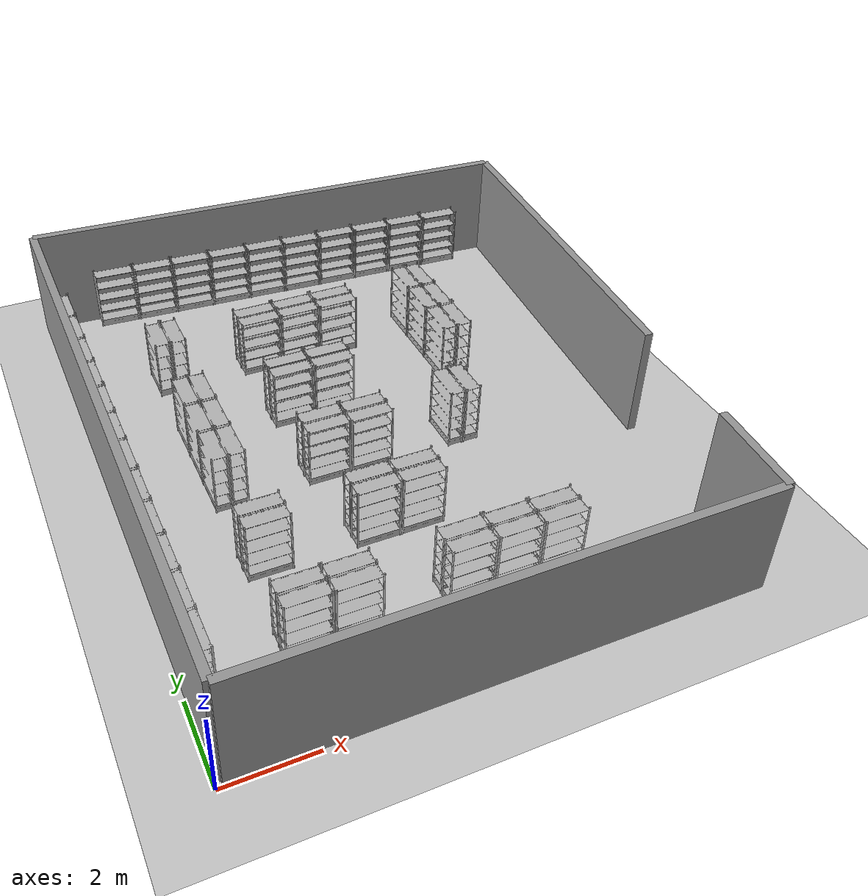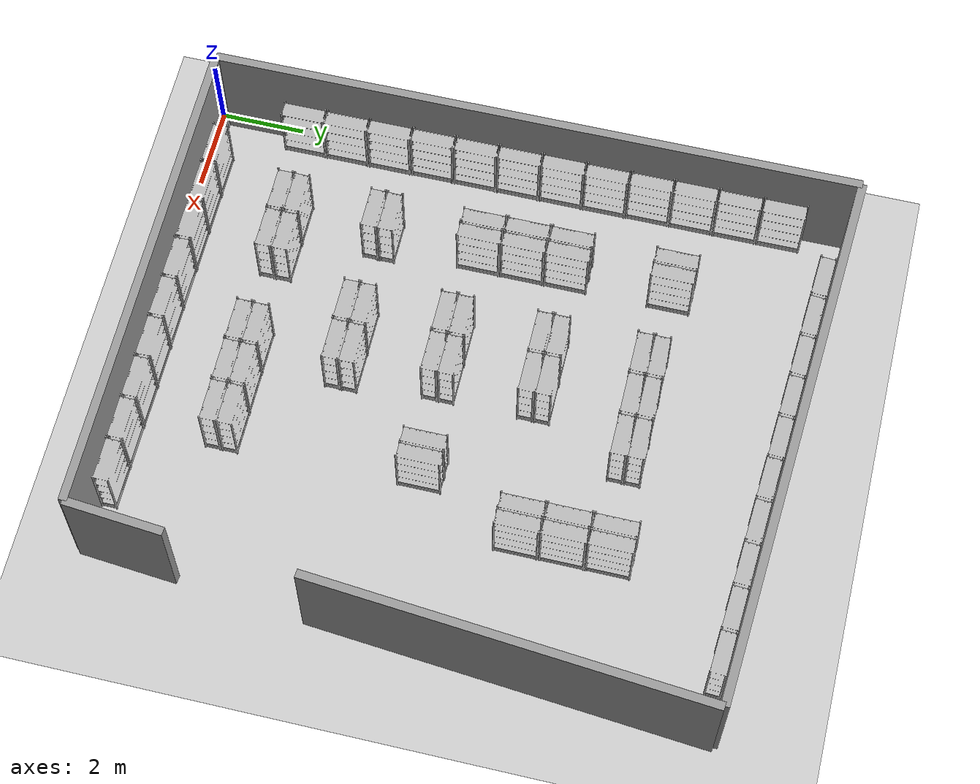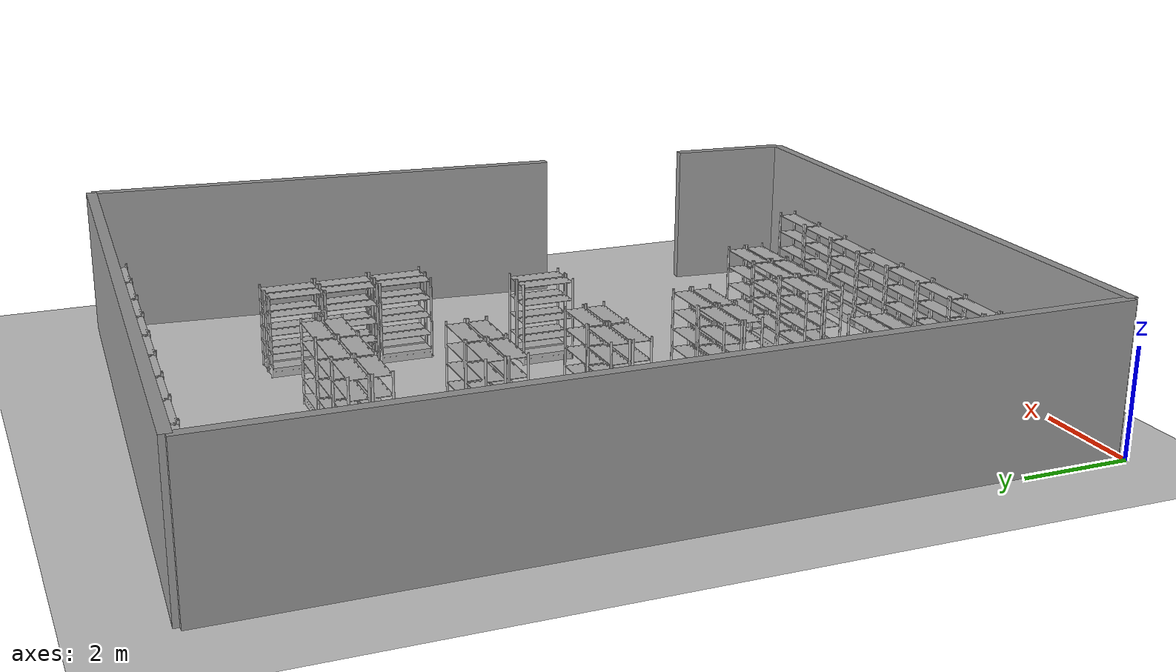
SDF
<sdf version="1.6">
  <world name="default">
    <light name="sun" type="directional">
      <cast_shadows>1</cast_shadows>
      <pose frame="">0 0 10 0 -0 0</pose>
      <diffuse>0.8 0.8 0.8 1</diffuse>
      <specular>0.2 0.2 0.2 1</specular>
      <attenuation>
        <range>1000</range>
        <constant>0.9</constant>
        <linear>0.01</linear>
        <quadratic>0.001</quadratic>
      </attenuation>
      <direction>-0.5 0.1 -0.9</direction>
    </light>
    <model name="ground_plane">
      <static>1</static>
      <link name="link">
        <collision name="collision">
          <geometry>
            <plane>
              <normal>0 0 1</normal>
              <size>100 100</size>
            </plane>
          </geometry>
          <surface>
            <contact>
              <collide_bitmask>65535</collide_bitmask>
              <ode />
            </contact>
            <friction>
              <ode>
                <mu>1000</mu>
                <mu2>1000</mu2>
              </ode>
              <torsional>
                <ode />
              </torsional>
            </friction>
            <bounce />
          </surface>
          <max_contacts>10</max_contacts>
        </collision>
        <visual name="visual">
          <cast_shadows>0</cast_shadows>
          <geometry>
            <plane>
              <normal>0 0 1</normal>
              <size>100 100</size>
            </plane>
          </geometry>
          <material>
            <script>
              <uri>file://media/materials/scripts/gazebo.material</uri>
              <name>Gazebo/Grey</name>
            </script>
          </material>
        </visual>
        <self_collide>0</self_collide>
        <enable_wind>0</enable_wind>
        <kinematic>0</kinematic>
      </link>
    </model>
    <gravity>0 0 -9.8</gravity>
    <magnetic_field>6e-06 2.3e-05 -4.2e-05</magnetic_field>
    <atmosphere type="adiabatic" />
    <physics name="default_physics" default="0" type="ode">
      <max_step_size>0.001</max_step_size>
      <real_time_factor>1</real_time_factor>
      <real_time_update_rate>1000</real_time_update_rate>
    </physics>
    <scene>
      <ambient>0.4 0.4 0.4 1</ambient>
      <background>0.7 0.7 0.7 1</background>
      <shadows>1</shadows>
    </scene>
    <audio>
      <device>default</device>
    </audio>
    <wind />
    <spherical_coordinates>
      <surface_model>EARTH_WGS84</surface_model>
      <latitude_deg>0</latitude_deg>
      <longitude_deg>0</longitude_deg>
      <elevation>0</elevation>
      <heading_deg>0</heading_deg>
    </spherical_coordinates>
    <gui fullscreen="0">
      <camera name="user_camera">
        <pose frame="">5.5458 -17.3868 19.7357 0 0.841797 1.67218</pose>
        <view_controller>orbit</view_controller>
        <projection_type>perspective</projection_type>
      </camera>
    </gui>
    <plugin name="ActorPosesPlugin" filename="libActorPosesPlugin.so" />
    <model name="store_shelf_moduled_0">
      <link name="link">
        <collision name="collision">
          <geometry>
            <mesh>
              <uri>model://store_shelf_moduled/meshes/store_shelf_moduled.dae</uri>
            </mesh>
          </geometry>
        </collision>
        <visual name="visual">
          <geometry>
            <mesh>
              <uri>model://store_shelf_moduled/meshes/store_shelf_moduled.dae</uri>
            </mesh>
          </geometry>
        </visual>
        <inertial>
          <mass>1000</mass>
          <inertia>
            <ixx>840083</ixx>
            <ixy>0</ixy>
            <ixz>0</ixz>
            <iyy>475500</iyy>
            <iyz>0</iyz>
            <izz>1.30208e+06</izz>
          </inertia>
        </inertial>
        <self_collide>0</self_collide>
        <enable_wind>0</enable_wind>
        <kinematic>0</kinematic>
      </link>
      <static>1</static>
      <pose frame="">1.180256 0.2199997 0 0 0 -0.002564097</pose>
    </model>
    <model name="store_shelf_moduled_1">
      <link name="link">
        <collision name="collision">
          <geometry>
            <mesh>
              <uri>model://store_shelf_moduled/meshes/store_shelf_moduled.dae</uri>
            </mesh>
          </geometry>
        </collision>
        <visual name="visual">
          <geometry>
            <mesh>
              <uri>model://store_shelf_moduled/meshes/store_shelf_moduled.dae</uri>
            </mesh>
          </geometry>
        </visual>
        <inertial>
          <mass>1000</mass>
          <inertia>
            <ixx>840083</ixx>
            <ixy>0</ixy>
            <ixz>0</ixz>
            <iyy>475500</iyy>
            <iyz>0</iyz>
            <izz>1.30208e+06</izz>
          </inertia>
        </inertial>
        <self_collide>0</self_collide>
        <enable_wind>0</enable_wind>
        <kinematic>0</kinematic>
      </link>
      <static>1</static>
      <pose frame="">2.240256 0.2199997 0 0 0 -0.002564097</pose>
    </model>
    <model name="store_shelf_moduled_2">
      <link name="link">
        <collision name="collision">
          <geometry>
            <mesh>
              <uri>model://store_shelf_moduled/meshes/store_shelf_moduled.dae</uri>
            </mesh>
          </geometry>
        </collision>
        <visual name="visual">
          <geometry>
            <mesh>
              <uri>model://store_shelf_moduled/meshes/store_shelf_moduled.dae</uri>
            </mesh>
          </geometry>
        </visual>
        <inertial>
          <mass>1000</mass>
          <inertia>
            <ixx>840083</ixx>
            <ixy>0</ixy>
            <ixz>0</ixz>
            <iyy>475500</iyy>
            <iyz>0</iyz>
            <izz>1.30208e+06</izz>
          </inertia>
        </inertial>
        <self_collide>0</self_collide>
        <enable_wind>0</enable_wind>
        <kinematic>0</kinematic>
      </link>
      <static>1</static>
      <pose frame="">3.300256 0.2199997 0 0 0 -0.002564097</pose>
    </model>
    <model name="store_shelf_moduled_3">
      <link name="link">
        <collision name="collision">
          <geometry>
            <mesh>
              <uri>model://store_shelf_moduled/meshes/store_shelf_moduled.dae</uri>
            </mesh>
          </geometry>
        </collision>
        <visual name="visual">
          <geometry>
            <mesh>
              <uri>model://store_shelf_moduled/meshes/store_shelf_moduled.dae</uri>
            </mesh>
          </geometry>
        </visual>
        <inertial>
          <mass>1000</mass>
          <inertia>
            <ixx>840083</ixx>
            <ixy>0</ixy>
            <ixz>0</ixz>
            <iyy>475500</iyy>
            <iyz>0</iyz>
            <izz>1.30208e+06</izz>
          </inertia>
        </inertial>
        <self_collide>0</self_collide>
        <enable_wind>0</enable_wind>
        <kinematic>0</kinematic>
      </link>
      <static>1</static>
      <pose frame="">4.360256 0.2099997 0 0 0 -0.002564097</pose>
    </model>
    <model name="store_shelf_moduled_4">
      <link name="link">
        <collision name="collision">
          <geometry>
            <mesh>
              <uri>model://store_shelf_moduled/meshes/store_shelf_moduled.dae</uri>
            </mesh>
          </geometry>
        </collision>
        <visual name="visual">
          <geometry>
            <mesh>
              <uri>model://store_shelf_moduled/meshes/store_shelf_moduled.dae</uri>
            </mesh>
          </geometry>
        </visual>
        <inertial>
          <mass>1000</mass>
          <inertia>
            <ixx>840083</ixx>
            <ixy>0</ixy>
            <ixz>0</ixz>
            <iyy>475500</iyy>
            <iyz>0</iyz>
            <izz>1.30208e+06</izz>
          </inertia>
        </inertial>
        <self_collide>0</self_collide>
        <enable_wind>0</enable_wind>
        <kinematic>0</kinematic>
      </link>
      <static>1</static>
      <pose frame="">5.420256 0.2099997 0 0 0 -0.002564097</pose>
    </model>
    <model name="store_shelf_moduled_5">
      <link name="link">
        <collision name="collision">
          <geometry>
            <mesh>
              <uri>model://store_shelf_moduled/meshes/store_shelf_moduled.dae</uri>
            </mesh>
          </geometry>
        </collision>
        <visual name="visual">
          <geometry>
            <mesh>
              <uri>model://store_shelf_moduled/meshes/store_shelf_moduled.dae</uri>
            </mesh>
          </geometry>
        </visual>
        <inertial>
          <mass>1000</mass>
          <inertia>
            <ixx>840083</ixx>
            <ixy>0</ixy>
            <ixz>0</ixz>
            <iyy>475500</iyy>
            <iyz>0</iyz>
            <izz>1.30208e+06</izz>
          </inertia>
        </inertial>
        <self_collide>0</self_collide>
        <enable_wind>0</enable_wind>
        <kinematic>0</kinematic>
      </link>
      <static>1</static>
      <pose frame="">6.480257 0.2099997 0 0 0 -0.002564097</pose>
    </model>
    <model name="store_shelf_moduled_6">
      <link name="link">
        <collision name="collision">
          <geometry>
            <mesh>
              <uri>model://store_shelf_moduled/meshes/store_shelf_moduled.dae</uri>
            </mesh>
          </geometry>
        </collision>
        <visual name="visual">
          <geometry>
            <mesh>
              <uri>model://store_shelf_moduled/meshes/store_shelf_moduled.dae</uri>
            </mesh>
          </geometry>
        </visual>
        <inertial>
          <mass>1000</mass>
          <inertia>
            <ixx>840083</ixx>
            <ixy>0</ixy>
            <ixz>0</ixz>
            <iyy>475500</iyy>
            <iyz>0</iyz>
            <izz>1.30208e+06</izz>
          </inertia>
        </inertial>
        <self_collide>0</self_collide>
        <enable_wind>0</enable_wind>
        <kinematic>0</kinematic>
      </link>
      <static>1</static>
      <pose frame="">7.540257 0.2099997 0 0 0 -0.002564097</pose>
    </model>
    <model name="store_shelf_moduled_7">
      <link name="link">
        <collision name="collision">
          <geometry>
            <mesh>
              <uri>model://store_shelf_moduled/meshes/store_shelf_moduled.dae</uri>
            </mesh>
          </geometry>
        </collision>
        <visual name="visual">
          <geometry>
            <mesh>
              <uri>model://store_shelf_moduled/meshes/store_shelf_moduled.dae</uri>
            </mesh>
          </geometry>
        </visual>
        <inertial>
          <mass>1000</mass>
          <inertia>
            <ixx>840083</ixx>
            <ixy>0</ixy>
            <ixz>0</ixz>
            <iyy>475500</iyy>
            <iyz>0</iyz>
            <izz>1.30208e+06</izz>
          </inertia>
        </inertial>
        <self_collide>0</self_collide>
        <enable_wind>0</enable_wind>
        <kinematic>0</kinematic>
      </link>
      <static>1</static>
      <pose frame="">8.600256 0.1999997 0 0 0 -0.002564097</pose>
    </model>
    <model name="store_shelf_moduled_8">
      <link name="link">
        <collision name="collision">
          <geometry>
            <mesh>
              <uri>model://store_shelf_moduled/meshes/store_shelf_moduled.dae</uri>
            </mesh>
          </geometry>
        </collision>
        <visual name="visual">
          <geometry>
            <mesh>
              <uri>model://store_shelf_moduled/meshes/store_shelf_moduled.dae</uri>
            </mesh>
          </geometry>
        </visual>
        <inertial>
          <mass>1000</mass>
          <inertia>
            <ixx>840083</ixx>
            <ixy>0</ixy>
            <ixz>0</ixz>
            <iyy>475500</iyy>
            <iyz>0</iyz>
            <izz>1.30208e+06</izz>
          </inertia>
        </inertial>
        <self_collide>0</self_collide>
        <enable_wind>0</enable_wind>
        <kinematic>0</kinematic>
      </link>
      <static>1</static>
      <pose frame="">9.660256 0.1999997 0 0 0 -0.002564097</pose>
    </model>
    <model name="store_shelf_moduled_9">
      <link name="link">
        <collision name="collision">
          <geometry>
            <mesh>
              <uri>model://store_shelf_moduled/meshes/store_shelf_moduled.dae</uri>
            </mesh>
          </geometry>
        </collision>
        <visual name="visual">
          <geometry>
            <mesh>
              <uri>model://store_shelf_moduled/meshes/store_shelf_moduled.dae</uri>
            </mesh>
          </geometry>
        </visual>
        <inertial>
          <mass>1000</mass>
          <inertia>
            <ixx>840083</ixx>
            <ixy>0</ixy>
            <ixz>0</ixz>
            <iyy>475500</iyy>
            <iyz>0</iyz>
            <izz>1.30208e+06</izz>
          </inertia>
        </inertial>
        <self_collide>0</self_collide>
        <enable_wind>0</enable_wind>
        <kinematic>0</kinematic>
      </link>
      <static>1</static>
      <pose frame="">12.02416 14.70017 0 0 0 3.083153</pose>
    </model>
    <model name="store_shelf_moduled_10">
      <link name="link">
        <collision name="collision">
          <geometry>
            <mesh>
              <uri>model://store_shelf_moduled/meshes/store_shelf_moduled.dae</uri>
            </mesh>
          </geometry>
        </collision>
        <visual name="visual">
          <geometry>
            <mesh>
              <uri>model://store_shelf_moduled/meshes/store_shelf_moduled.dae</uri>
            </mesh>
          </geometry>
        </visual>
        <inertial>
          <mass>1000</mass>
          <inertia>
            <ixx>840083</ixx>
            <ixy>0</ixy>
            <ixz>0</ixz>
            <iyy>475500</iyy>
            <iyz>0</iyz>
            <izz>1.30208e+06</izz>
          </inertia>
        </inertial>
        <self_collide>0</self_collide>
        <enable_wind>0</enable_wind>
        <kinematic>0</kinematic>
      </link>
      <static>1</static>
      <pose frame="">10.96416 14.76017 0 0 0 3.083153</pose>
    </model>
    <model name="store_shelf_moduled_11">
      <link name="link">
        <collision name="collision">
          <geometry>
            <mesh>
              <uri>model://store_shelf_moduled/meshes/store_shelf_moduled.dae</uri>
            </mesh>
          </geometry>
        </collision>
        <visual name="visual">
          <geometry>
            <mesh>
              <uri>model://store_shelf_moduled/meshes/store_shelf_moduled.dae</uri>
            </mesh>
          </geometry>
        </visual>
        <inertial>
          <mass>1000</mass>
          <inertia>
            <ixx>840083</ixx>
            <ixy>0</ixy>
            <ixz>0</ixz>
            <iyy>475500</iyy>
            <iyz>0</iyz>
            <izz>1.30208e+06</izz>
          </inertia>
        </inertial>
        <self_collide>0</self_collide>
        <enable_wind>0</enable_wind>
        <kinematic>0</kinematic>
      </link>
      <static>1</static>
      <pose frame="">9.90416 14.82017 0 0 0 3.083153</pose>
    </model>
    <model name="store_shelf_moduled_12">
      <link name="link">
        <collision name="collision">
          <geometry>
            <mesh>
              <uri>model://store_shelf_moduled/meshes/store_shelf_moduled.dae</uri>
            </mesh>
          </geometry>
        </collision>
        <visual name="visual">
          <geometry>
            <mesh>
              <uri>model://store_shelf_moduled/meshes/store_shelf_moduled.dae</uri>
            </mesh>
          </geometry>
        </visual>
        <inertial>
          <mass>1000</mass>
          <inertia>
            <ixx>840083</ixx>
            <ixy>0</ixy>
            <ixz>0</ixz>
            <iyy>475500</iyy>
            <iyz>0</iyz>
            <izz>1.30208e+06</izz>
          </inertia>
        </inertial>
        <self_collide>0</self_collide>
        <enable_wind>0</enable_wind>
        <kinematic>0</kinematic>
      </link>
      <static>1</static>
      <pose frame="">8.844159 14.88017 0 0 0 3.083153</pose>
    </model>
    <model name="store_shelf_moduled_13">
      <link name="link">
        <collision name="collision">
          <geometry>
            <mesh>
              <uri>model://store_shelf_moduled/meshes/store_shelf_moduled.dae</uri>
            </mesh>
          </geometry>
        </collision>
        <visual name="visual">
          <geometry>
            <mesh>
              <uri>model://store_shelf_moduled/meshes/store_shelf_moduled.dae</uri>
            </mesh>
          </geometry>
        </visual>
        <inertial>
          <mass>1000</mass>
          <inertia>
            <ixx>840083</ixx>
            <ixy>0</ixy>
            <ixz>0</ixz>
            <iyy>475500</iyy>
            <iyz>0</iyz>
            <izz>1.30208e+06</izz>
          </inertia>
        </inertial>
        <self_collide>0</self_collide>
        <enable_wind>0</enable_wind>
        <kinematic>0</kinematic>
      </link>
      <static>1</static>
      <pose frame="">7.78416 14.94017 0 0 0 3.083153</pose>
    </model>
    <model name="store_shelf_moduled_14">
      <link name="link">
        <collision name="collision">
          <geometry>
            <mesh>
              <uri>model://store_shelf_moduled/meshes/store_shelf_moduled.dae</uri>
            </mesh>
          </geometry>
        </collision>
        <visual name="visual">
          <geometry>
            <mesh>
              <uri>model://store_shelf_moduled/meshes/store_shelf_moduled.dae</uri>
            </mesh>
          </geometry>
        </visual>
        <inertial>
          <mass>1000</mass>
          <inertia>
            <ixx>840083</ixx>
            <ixy>0</ixy>
            <ixz>0</ixz>
            <iyy>475500</iyy>
            <iyz>0</iyz>
            <izz>1.30208e+06</izz>
          </inertia>
        </inertial>
        <self_collide>0</self_collide>
        <enable_wind>0</enable_wind>
        <kinematic>0</kinematic>
      </link>
      <static>1</static>
      <pose frame="">6.734159 15.01017 0 0 0 3.083153</pose>
    </model>
    <model name="store_shelf_moduled_15">
      <link name="link">
        <collision name="collision">
          <geometry>
            <mesh>
              <uri>model://store_shelf_moduled/meshes/store_shelf_moduled.dae</uri>
            </mesh>
          </geometry>
        </collision>
        <visual name="visual">
          <geometry>
            <mesh>
              <uri>model://store_shelf_moduled/meshes/store_shelf_moduled.dae</uri>
            </mesh>
          </geometry>
        </visual>
        <inertial>
          <mass>1000</mass>
          <inertia>
            <ixx>840083</ixx>
            <ixy>0</ixy>
            <ixz>0</ixz>
            <iyy>475500</iyy>
            <iyz>0</iyz>
            <izz>1.30208e+06</izz>
          </inertia>
        </inertial>
        <self_collide>0</self_collide>
        <enable_wind>0</enable_wind>
        <kinematic>0</kinematic>
      </link>
      <static>1</static>
      <pose frame="">5.67416 15.07017 0 0 0 3.083153</pose>
    </model>
    <model name="store_shelf_moduled_16">
      <link name="link">
        <collision name="collision">
          <geometry>
            <mesh>
              <uri>model://store_shelf_moduled/meshes/store_shelf_moduled.dae</uri>
            </mesh>
          </geometry>
        </collision>
        <visual name="visual">
          <geometry>
            <mesh>
              <uri>model://store_shelf_moduled/meshes/store_shelf_moduled.dae</uri>
            </mesh>
          </geometry>
        </visual>
        <inertial>
          <mass>1000</mass>
          <inertia>
            <ixx>840083</ixx>
            <ixy>0</ixy>
            <ixz>0</ixz>
            <iyy>475500</iyy>
            <iyz>0</iyz>
            <izz>1.30208e+06</izz>
          </inertia>
        </inertial>
        <self_collide>0</self_collide>
        <enable_wind>0</enable_wind>
        <kinematic>0</kinematic>
      </link>
      <static>1</static>
      <pose frame="">4.614159 15.13017 0 0 0 3.083153</pose>
    </model>
    <model name="store_shelf_moduled_17">
      <link name="link">
        <collision name="collision">
          <geometry>
            <mesh>
              <uri>model://store_shelf_moduled/meshes/store_shelf_moduled.dae</uri>
            </mesh>
          </geometry>
        </collision>
        <visual name="visual">
          <geometry>
            <mesh>
              <uri>model://store_shelf_moduled/meshes/store_shelf_moduled.dae</uri>
            </mesh>
          </geometry>
        </visual>
        <inertial>
          <mass>1000</mass>
          <inertia>
            <ixx>840083</ixx>
            <ixy>0</ixy>
            <ixz>0</ixz>
            <iyy>475500</iyy>
            <iyz>0</iyz>
            <izz>1.30208e+06</izz>
          </inertia>
        </inertial>
        <self_collide>0</self_collide>
        <enable_wind>0</enable_wind>
        <kinematic>0</kinematic>
      </link>
      <static>1</static>
      <pose frame="">3.554159 15.19017 0 0 0 3.083153</pose>
    </model>
    <model name="store_shelf_moduled_18">
      <link name="link">
        <collision name="collision">
          <geometry>
            <mesh>
              <uri>model://store_shelf_moduled/meshes/store_shelf_moduled.dae</uri>
            </mesh>
          </geometry>
        </collision>
        <visual name="visual">
          <geometry>
            <mesh>
              <uri>model://store_shelf_moduled/meshes/store_shelf_moduled.dae</uri>
            </mesh>
          </geometry>
        </visual>
        <inertial>
          <mass>1000</mass>
          <inertia>
            <ixx>840083</ixx>
            <ixy>0</ixy>
            <ixz>0</ixz>
            <iyy>475500</iyy>
            <iyz>0</iyz>
            <izz>1.30208e+06</izz>
          </inertia>
        </inertial>
        <self_collide>0</self_collide>
        <enable_wind>0</enable_wind>
        <kinematic>0</kinematic>
      </link>
      <static>1</static>
      <pose frame="">2.494159 15.25017 0 0 0 3.083153</pose>
    </model>
    <model name="store_shelf_moduled_19">
      <link name="link">
        <collision name="collision">
          <geometry>
            <mesh>
              <uri>model://store_shelf_moduled/meshes/store_shelf_moduled.dae</uri>
            </mesh>
          </geometry>
        </collision>
        <visual name="visual">
          <geometry>
            <mesh>
              <uri>model://store_shelf_moduled/meshes/store_shelf_moduled.dae</uri>
            </mesh>
          </geometry>
        </visual>
        <inertial>
          <mass>1000</mass>
          <inertia>
            <ixx>840083</ixx>
            <ixy>0</ixy>
            <ixz>0</ixz>
            <iyy>475500</iyy>
            <iyz>0</iyz>
            <izz>1.30208e+06</izz>
          </inertia>
        </inertial>
        <self_collide>0</self_collide>
        <enable_wind>0</enable_wind>
        <kinematic>0</kinematic>
      </link>
      <static>1</static>
      <pose frame="">0.1999998 14.4402 0 0 0 -1.568844</pose>
    </model>
    <model name="store_shelf_moduled_20">
      <link name="link">
        <collision name="collision">
          <geometry>
            <mesh>
              <uri>model://store_shelf_moduled/meshes/store_shelf_moduled.dae</uri>
            </mesh>
          </geometry>
        </collision>
        <visual name="visual">
          <geometry>
            <mesh>
              <uri>model://store_shelf_moduled/meshes/store_shelf_moduled.dae</uri>
            </mesh>
          </geometry>
        </visual>
        <inertial>
          <mass>1000</mass>
          <inertia>
            <ixx>840083</ixx>
            <ixy>0</ixy>
            <ixz>0</ixz>
            <iyy>475500</iyy>
            <iyz>0</iyz>
            <izz>1.30208e+06</izz>
          </inertia>
        </inertial>
        <self_collide>0</self_collide>
        <enable_wind>0</enable_wind>
        <kinematic>0</kinematic>
      </link>
      <static>1</static>
      <pose frame="">0.1999998 13.3802 0 0 0 -1.568844</pose>
    </model>
    <model name="store_shelf_moduled_21">
      <link name="link">
        <collision name="collision">
          <geometry>
            <mesh>
              <uri>model://store_shelf_moduled/meshes/store_shelf_moduled.dae</uri>
            </mesh>
          </geometry>
        </collision>
        <visual name="visual">
          <geometry>
            <mesh>
              <uri>model://store_shelf_moduled/meshes/store_shelf_moduled.dae</uri>
            </mesh>
          </geometry>
        </visual>
        <inertial>
          <mass>1000</mass>
          <inertia>
            <ixx>840083</ixx>
            <ixy>0</ixy>
            <ixz>0</ixz>
            <iyy>475500</iyy>
            <iyz>0</iyz>
            <izz>1.30208e+06</izz>
          </inertia>
        </inertial>
        <self_collide>0</self_collide>
        <enable_wind>0</enable_wind>
        <kinematic>0</kinematic>
      </link>
      <static>1</static>
      <pose frame="">0.1999998 12.3202 0 0 0 -1.568844</pose>
    </model>
    <model name="store_shelf_moduled_22">
      <link name="link">
        <collision name="collision">
          <geometry>
            <mesh>
              <uri>model://store_shelf_moduled/meshes/store_shelf_moduled.dae</uri>
            </mesh>
          </geometry>
        </collision>
        <visual name="visual">
          <geometry>
            <mesh>
              <uri>model://store_shelf_moduled/meshes/store_shelf_moduled.dae</uri>
            </mesh>
          </geometry>
        </visual>
        <inertial>
          <mass>1000</mass>
          <inertia>
            <ixx>840083</ixx>
            <ixy>0</ixy>
            <ixz>0</ixz>
            <iyy>475500</iyy>
            <iyz>0</iyz>
            <izz>1.30208e+06</izz>
          </inertia>
        </inertial>
        <self_collide>0</self_collide>
        <enable_wind>0</enable_wind>
        <kinematic>0</kinematic>
      </link>
      <static>1</static>
      <pose frame="">0.1999998 11.2602 0 0 0 -1.568844</pose>
    </model>
    <model name="store_shelf_moduled_23">
      <link name="link">
        <collision name="collision">
          <geometry>
            <mesh>
              <uri>model://store_shelf_moduled/meshes/store_shelf_moduled.dae</uri>
            </mesh>
          </geometry>
        </collision>
        <visual name="visual">
          <geometry>
            <mesh>
              <uri>model://store_shelf_moduled/meshes/store_shelf_moduled.dae</uri>
            </mesh>
          </geometry>
        </visual>
        <inertial>
          <mass>1000</mass>
          <inertia>
            <ixx>840083</ixx>
            <ixy>0</ixy>
            <ixz>0</ixz>
            <iyy>475500</iyy>
            <iyz>0</iyz>
            <izz>1.30208e+06</izz>
          </inertia>
        </inertial>
        <self_collide>0</self_collide>
        <enable_wind>0</enable_wind>
        <kinematic>0</kinematic>
      </link>
      <static>1</static>
      <pose frame="">0.2099998 10.2002 0 0 0 -1.568844</pose>
    </model>
    <model name="store_shelf_moduled_24">
      <link name="link">
        <collision name="collision">
          <geometry>
            <mesh>
              <uri>model://store_shelf_moduled/meshes/store_shelf_moduled.dae</uri>
            </mesh>
          </geometry>
        </collision>
        <visual name="visual">
          <geometry>
            <mesh>
              <uri>model://store_shelf_moduled/meshes/store_shelf_moduled.dae</uri>
            </mesh>
          </geometry>
        </visual>
        <inertial>
          <mass>1000</mass>
          <inertia>
            <ixx>840083</ixx>
            <ixy>0</ixy>
            <ixz>0</ixz>
            <iyy>475500</iyy>
            <iyz>0</iyz>
            <izz>1.30208e+06</izz>
          </inertia>
        </inertial>
        <self_collide>0</self_collide>
        <enable_wind>0</enable_wind>
        <kinematic>0</kinematic>
      </link>
      <static>1</static>
      <pose frame="">0.2099998 9.140195 0 0 0 -1.568844</pose>
    </model>
    <model name="store_shelf_moduled_25">
      <link name="link">
        <collision name="collision">
          <geometry>
            <mesh>
              <uri>model://store_shelf_moduled/meshes/store_shelf_moduled.dae</uri>
            </mesh>
          </geometry>
        </collision>
        <visual name="visual">
          <geometry>
            <mesh>
              <uri>model://store_shelf_moduled/meshes/store_shelf_moduled.dae</uri>
            </mesh>
          </geometry>
        </visual>
        <inertial>
          <mass>1000</mass>
          <inertia>
            <ixx>840083</ixx>
            <ixy>0</ixy>
            <ixz>0</ixz>
            <iyy>475500</iyy>
            <iyz>0</iyz>
            <izz>1.30208e+06</izz>
          </inertia>
        </inertial>
        <self_collide>0</self_collide>
        <enable_wind>0</enable_wind>
        <kinematic>0</kinematic>
      </link>
      <static>1</static>
      <pose frame="">0.2099998 8.080195 0 0 0 -1.568844</pose>
    </model>
    <model name="store_shelf_moduled_26">
      <link name="link">
        <collision name="collision">
          <geometry>
            <mesh>
              <uri>model://store_shelf_moduled/meshes/store_shelf_moduled.dae</uri>
            </mesh>
          </geometry>
        </collision>
        <visual name="visual">
          <geometry>
            <mesh>
              <uri>model://store_shelf_moduled/meshes/store_shelf_moduled.dae</uri>
            </mesh>
          </geometry>
        </visual>
        <inertial>
          <mass>1000</mass>
          <inertia>
            <ixx>840083</ixx>
            <ixy>0</ixy>
            <ixz>0</ixz>
            <iyy>475500</iyy>
            <iyz>0</iyz>
            <izz>1.30208e+06</izz>
          </inertia>
        </inertial>
        <self_collide>0</self_collide>
        <enable_wind>0</enable_wind>
        <kinematic>0</kinematic>
      </link>
      <static>1</static>
      <pose frame="">0.2099998 7.020195 0 0 0 -1.568844</pose>
    </model>
    <model name="store_shelf_moduled_27">
      <link name="link">
        <collision name="collision">
          <geometry>
            <mesh>
              <uri>model://store_shelf_moduled/meshes/store_shelf_moduled.dae</uri>
            </mesh>
          </geometry>
        </collision>
        <visual name="visual">
          <geometry>
            <mesh>
              <uri>model://store_shelf_moduled/meshes/store_shelf_moduled.dae</uri>
            </mesh>
          </geometry>
        </visual>
        <inertial>
          <mass>1000</mass>
          <inertia>
            <ixx>840083</ixx>
            <ixy>0</ixy>
            <ixz>0</ixz>
            <iyy>475500</iyy>
            <iyz>0</iyz>
            <izz>1.30208e+06</izz>
          </inertia>
        </inertial>
        <self_collide>0</self_collide>
        <enable_wind>0</enable_wind>
        <kinematic>0</kinematic>
      </link>
      <static>1</static>
      <pose frame="">0.2099998 5.960196 0 0 0 -1.568844</pose>
    </model>
    <model name="store_shelf_moduled_28">
      <link name="link">
        <collision name="collision">
          <geometry>
            <mesh>
              <uri>model://store_shelf_moduled/meshes/store_shelf_moduled.dae</uri>
            </mesh>
          </geometry>
        </collision>
        <visual name="visual">
          <geometry>
            <mesh>
              <uri>model://store_shelf_moduled/meshes/store_shelf_moduled.dae</uri>
            </mesh>
          </geometry>
        </visual>
        <inertial>
          <mass>1000</mass>
          <inertia>
            <ixx>840083</ixx>
            <ixy>0</ixy>
            <ixz>0</ixz>
            <iyy>475500</iyy>
            <iyz>0</iyz>
            <izz>1.30208e+06</izz>
          </inertia>
        </inertial>
        <self_collide>0</self_collide>
        <enable_wind>0</enable_wind>
        <kinematic>0</kinematic>
      </link>
      <static>1</static>
      <pose frame="">0.2199998 4.900195 0 0 0 -1.568844</pose>
    </model>
    <model name="store_shelf_moduled_29">
      <link name="link">
        <collision name="collision">
          <geometry>
            <mesh>
              <uri>model://store_shelf_moduled/meshes/store_shelf_moduled.dae</uri>
            </mesh>
          </geometry>
        </collision>
        <visual name="visual">
          <geometry>
            <mesh>
              <uri>model://store_shelf_moduled/meshes/store_shelf_moduled.dae</uri>
            </mesh>
          </geometry>
        </visual>
        <inertial>
          <mass>1000</mass>
          <inertia>
            <ixx>840083</ixx>
            <ixy>0</ixy>
            <ixz>0</ixz>
            <iyy>475500</iyy>
            <iyz>0</iyz>
            <izz>1.30208e+06</izz>
          </inertia>
        </inertial>
        <self_collide>0</self_collide>
        <enable_wind>0</enable_wind>
        <kinematic>0</kinematic>
      </link>
      <static>1</static>
      <pose frame="">0.2199998 3.840195 0 0 0 -1.568844</pose>
    </model>
    <model name="store_shelf_moduled_30">
      <link name="link">
        <collision name="collision">
          <geometry>
            <mesh>
              <uri>model://store_shelf_moduled/meshes/store_shelf_moduled.dae</uri>
            </mesh>
          </geometry>
        </collision>
        <visual name="visual">
          <geometry>
            <mesh>
              <uri>model://store_shelf_moduled/meshes/store_shelf_moduled.dae</uri>
            </mesh>
          </geometry>
        </visual>
        <inertial>
          <mass>1000</mass>
          <inertia>
            <ixx>840083</ixx>
            <ixy>0</ixy>
            <ixz>0</ixz>
            <iyy>475500</iyy>
            <iyz>0</iyz>
            <izz>1.30208e+06</izz>
          </inertia>
        </inertial>
        <self_collide>0</self_collide>
        <enable_wind>0</enable_wind>
        <kinematic>0</kinematic>
      </link>
      <static>1</static>
      <pose frame="">0.2199998 2.780195 0 0 0 -1.568844</pose>
    </model>
    <model name="store_shelf_moduled_31">
      <link name="link">
        <collision name="collision">
          <geometry>
            <mesh>
              <uri>model://store_shelf_moduled/meshes/store_shelf_moduled.dae</uri>
            </mesh>
          </geometry>
        </collision>
        <visual name="visual">
          <geometry>
            <mesh>
              <uri>model://store_shelf_moduled/meshes/store_shelf_moduled.dae</uri>
            </mesh>
          </geometry>
        </visual>
        <inertial>
          <mass>1000</mass>
          <inertia>
            <ixx>840083</ixx>
            <ixy>0</ixy>
            <ixz>0</ixz>
            <iyy>475500</iyy>
            <iyz>0</iyz>
            <izz>1.30208e+06</izz>
          </inertia>
        </inertial>
        <self_collide>0</self_collide>
        <enable_wind>0</enable_wind>
        <kinematic>0</kinematic>
      </link>
      <static>1</static>
      <pose frame="">2.05 2.47 0 0 0 0</pose>
    </model>
    <model name="store_shelf_moduled_32">
      <link name="link">
        <collision name="collision">
          <geometry>
            <mesh>
              <uri>model://store_shelf_moduled/meshes/store_shelf_moduled.dae</uri>
            </mesh>
          </geometry>
        </collision>
        <visual name="visual">
          <geometry>
            <mesh>
              <uri>model://store_shelf_moduled/meshes/store_shelf_moduled.dae</uri>
            </mesh>
          </geometry>
        </visual>
        <inertial>
          <mass>1000</mass>
          <inertia>
            <ixx>840083</ixx>
            <ixy>0</ixy>
            <ixz>0</ixz>
            <iyy>475500</iyy>
            <iyz>0</iyz>
            <izz>1.30208e+06</izz>
          </inertia>
        </inertial>
        <self_collide>0</self_collide>
        <enable_wind>0</enable_wind>
        <kinematic>0</kinematic>
      </link>
      <static>1</static>
      <pose frame="">3.11 2.47 0 0 0 -3.141593</pose>
    </model>
    <model name="store_shelf_moduled_33">
      <link name="link">
        <collision name="collision">
          <geometry>
            <mesh>
              <uri>model://store_shelf_moduled/meshes/store_shelf_moduled.dae</uri>
            </mesh>
          </geometry>
        </collision>
        <visual name="visual">
          <geometry>
            <mesh>
              <uri>model://store_shelf_moduled/meshes/store_shelf_moduled.dae</uri>
            </mesh>
          </geometry>
        </visual>
        <inertial>
          <mass>1000</mass>
          <inertia>
            <ixx>840083</ixx>
            <ixy>0</ixy>
            <ixz>0</ixz>
            <iyy>475500</iyy>
            <iyz>0</iyz>
            <izz>1.30208e+06</izz>
          </inertia>
        </inertial>
        <self_collide>0</self_collide>
        <enable_wind>0</enable_wind>
        <kinematic>0</kinematic>
      </link>
      <static>1</static>
      <pose frame="">3.11 2.47 0 0 0 0</pose>
    </model>
    <model name="store_shelf_moduled_34">
      <link name="link">
        <collision name="collision">
          <geometry>
            <mesh>
              <uri>model://store_shelf_moduled/meshes/store_shelf_moduled.dae</uri>
            </mesh>
          </geometry>
        </collision>
        <visual name="visual">
          <geometry>
            <mesh>
              <uri>model://store_shelf_moduled/meshes/store_shelf_moduled.dae</uri>
            </mesh>
          </geometry>
        </visual>
        <inertial>
          <mass>1000</mass>
          <inertia>
            <ixx>840083</ixx>
            <ixy>0</ixy>
            <ixz>0</ixz>
            <iyy>475500</iyy>
            <iyz>0</iyz>
            <izz>1.30208e+06</izz>
          </inertia>
        </inertial>
        <self_collide>0</self_collide>
        <enable_wind>0</enable_wind>
        <kinematic>0</kinematic>
      </link>
      <static>1</static>
      <pose frame="">4.17 2.47 0 0 0 -3.141593</pose>
    </model>
    <model name="store_shelf_moduled_35">
      <link name="link">
        <collision name="collision">
          <geometry>
            <mesh>
              <uri>model://store_shelf_moduled/meshes/store_shelf_moduled.dae</uri>
            </mesh>
          </geometry>
        </collision>
        <visual name="visual">
          <geometry>
            <mesh>
              <uri>model://store_shelf_moduled/meshes/store_shelf_moduled.dae</uri>
            </mesh>
          </geometry>
        </visual>
        <inertial>
          <mass>1000</mass>
          <inertia>
            <ixx>840083</ixx>
            <ixy>0</ixy>
            <ixz>0</ixz>
            <iyy>475500</iyy>
            <iyz>0</iyz>
            <izz>1.30208e+06</izz>
          </inertia>
        </inertial>
        <self_collide>0</self_collide>
        <enable_wind>0</enable_wind>
        <kinematic>0</kinematic>
      </link>
      <static>1</static>
      <pose frame="">2.47 6.57 0 0 0 1.570796</pose>
    </model>
    <model name="store_shelf_moduled_36">
      <link name="link">
        <collision name="collision">
          <geometry>
            <mesh>
              <uri>model://store_shelf_moduled/meshes/store_shelf_moduled.dae</uri>
            </mesh>
          </geometry>
        </collision>
        <visual name="visual">
          <geometry>
            <mesh>
              <uri>model://store_shelf_moduled/meshes/store_shelf_moduled.dae</uri>
            </mesh>
          </geometry>
        </visual>
        <inertial>
          <mass>1000</mass>
          <inertia>
            <ixx>840083</ixx>
            <ixy>0</ixy>
            <ixz>0</ixz>
            <iyy>475500</iyy>
            <iyz>0</iyz>
            <izz>1.30208e+06</izz>
          </inertia>
        </inertial>
        <self_collide>0</self_collide>
        <enable_wind>0</enable_wind>
        <kinematic>0</kinematic>
      </link>
      <static>1</static>
      <pose frame="">2.47 7.63 0 0 0 -1.570796</pose>
    </model>
    <model name="store_shelf_moduled_37">
      <link name="link">
        <collision name="collision">
          <geometry>
            <mesh>
              <uri>model://store_shelf_moduled/meshes/store_shelf_moduled.dae</uri>
            </mesh>
          </geometry>
        </collision>
        <visual name="visual">
          <geometry>
            <mesh>
              <uri>model://store_shelf_moduled/meshes/store_shelf_moduled.dae</uri>
            </mesh>
          </geometry>
        </visual>
        <inertial>
          <mass>1000</mass>
          <inertia>
            <ixx>840083</ixx>
            <ixy>0</ixy>
            <ixz>0</ixz>
            <iyy>475500</iyy>
            <iyz>0</iyz>
            <izz>1.30208e+06</izz>
          </inertia>
        </inertial>
        <self_collide>0</self_collide>
        <enable_wind>0</enable_wind>
        <kinematic>0</kinematic>
      </link>
      <static>1</static>
      <pose frame="">2.47 7.63 0 0 0 1.570796</pose>
    </model>
    <model name="store_shelf_moduled_38">
      <link name="link">
        <collision name="collision">
          <geometry>
            <mesh>
              <uri>model://store_shelf_moduled/meshes/store_shelf_moduled.dae</uri>
            </mesh>
          </geometry>
        </collision>
        <visual name="visual">
          <geometry>
            <mesh>
              <uri>model://store_shelf_moduled/meshes/store_shelf_moduled.dae</uri>
            </mesh>
          </geometry>
        </visual>
        <inertial>
          <mass>1000</mass>
          <inertia>
            <ixx>840083</ixx>
            <ixy>0</ixy>
            <ixz>0</ixz>
            <iyy>475500</iyy>
            <iyz>0</iyz>
            <izz>1.30208e+06</izz>
          </inertia>
        </inertial>
        <self_collide>0</self_collide>
        <enable_wind>0</enable_wind>
        <kinematic>0</kinematic>
      </link>
      <static>1</static>
      <pose frame="">2.47 8.69 0 0 0 -1.570796</pose>
    </model>
    <model name="store_shelf_moduled_39">
      <link name="link">
        <collision name="collision">
          <geometry>
            <mesh>
              <uri>model://store_shelf_moduled/meshes/store_shelf_moduled.dae</uri>
            </mesh>
          </geometry>
        </collision>
        <visual name="visual">
          <geometry>
            <mesh>
              <uri>model://store_shelf_moduled/meshes/store_shelf_moduled.dae</uri>
            </mesh>
          </geometry>
        </visual>
        <inertial>
          <mass>1000</mass>
          <inertia>
            <ixx>840083</ixx>
            <ixy>0</ixy>
            <ixz>0</ixz>
            <iyy>475500</iyy>
            <iyz>0</iyz>
            <izz>1.30208e+06</izz>
          </inertia>
        </inertial>
        <self_collide>0</self_collide>
        <enable_wind>0</enable_wind>
        <kinematic>0</kinematic>
      </link>
      <static>1</static>
      <pose frame="">2.47 8.69 0 0 0 1.570796</pose>
    </model>
    <model name="store_shelf_moduled_40">
      <link name="link">
        <collision name="collision">
          <geometry>
            <mesh>
              <uri>model://store_shelf_moduled/meshes/store_shelf_moduled.dae</uri>
            </mesh>
          </geometry>
        </collision>
        <visual name="visual">
          <geometry>
            <mesh>
              <uri>model://store_shelf_moduled/meshes/store_shelf_moduled.dae</uri>
            </mesh>
          </geometry>
        </visual>
        <inertial>
          <mass>1000</mass>
          <inertia>
            <ixx>840083</ixx>
            <ixy>0</ixy>
            <ixz>0</ixz>
            <iyy>475500</iyy>
            <iyz>0</iyz>
            <izz>1.30208e+06</izz>
          </inertia>
        </inertial>
        <self_collide>0</self_collide>
        <enable_wind>0</enable_wind>
        <kinematic>0</kinematic>
      </link>
      <static>1</static>
      <pose frame="">2.47 9.75 0 0 0 -1.570796</pose>
    </model>
    <model name="store_shelf_moduled_41">
      <link name="link">
        <collision name="collision">
          <geometry>
            <mesh>
              <uri>model://store_shelf_moduled/meshes/store_shelf_moduled.dae</uri>
            </mesh>
          </geometry>
        </collision>
        <visual name="visual">
          <geometry>
            <mesh>
              <uri>model://store_shelf_moduled/meshes/store_shelf_moduled.dae</uri>
            </mesh>
          </geometry>
        </visual>
        <inertial>
          <mass>1000</mass>
          <inertia>
            <ixx>840083</ixx>
            <ixy>0</ixy>
            <ixz>0</ixz>
            <iyy>475500</iyy>
            <iyz>0</iyz>
            <izz>1.30208e+06</izz>
          </inertia>
        </inertial>
        <self_collide>0</self_collide>
        <enable_wind>0</enable_wind>
        <kinematic>0</kinematic>
      </link>
      <static>1</static>
      <pose frame="">2.05 4.73 0 0 0 0</pose>
    </model>
    <model name="store_shelf_moduled_42">
      <link name="link">
        <collision name="collision">
          <geometry>
            <mesh>
              <uri>model://store_shelf_moduled/meshes/store_shelf_moduled.dae</uri>
            </mesh>
          </geometry>
        </collision>
        <visual name="visual">
          <geometry>
            <mesh>
              <uri>model://store_shelf_moduled/meshes/store_shelf_moduled.dae</uri>
            </mesh>
          </geometry>
        </visual>
        <inertial>
          <mass>1000</mass>
          <inertia>
            <ixx>840083</ixx>
            <ixy>0</ixy>
            <ixz>0</ixz>
            <iyy>475500</iyy>
            <iyz>0</iyz>
            <izz>1.30208e+06</izz>
          </inertia>
        </inertial>
        <self_collide>0</self_collide>
        <enable_wind>0</enable_wind>
        <kinematic>0</kinematic>
      </link>
      <static>1</static>
      <pose frame="">3.11 4.73 0 0 0 -3.141593</pose>
    </model>
    <model name="store_shelf_moduled_43">
      <link name="link">
        <collision name="collision">
          <geometry>
            <mesh>
              <uri>model://store_shelf_moduled/meshes/store_shelf_moduled.dae</uri>
            </mesh>
          </geometry>
        </collision>
        <visual name="visual">
          <geometry>
            <mesh>
              <uri>model://store_shelf_moduled/meshes/store_shelf_moduled.dae</uri>
            </mesh>
          </geometry>
        </visual>
        <inertial>
          <mass>1000</mass>
          <inertia>
            <ixx>840083</ixx>
            <ixy>0</ixy>
            <ixz>0</ixz>
            <iyy>475500</iyy>
            <iyz>0</iyz>
            <izz>1.30208e+06</izz>
          </inertia>
        </inertial>
        <self_collide>0</self_collide>
        <enable_wind>0</enable_wind>
        <kinematic>0</kinematic>
      </link>
      <static>1</static>
      <pose frame="">2.47 11.17 0 0 0 1.570796</pose>
    </model>
    <model name="store_shelf_moduled_44">
      <link name="link">
        <collision name="collision">
          <geometry>
            <mesh>
              <uri>model://store_shelf_moduled/meshes/store_shelf_moduled.dae</uri>
            </mesh>
          </geometry>
        </collision>
        <visual name="visual">
          <geometry>
            <mesh>
              <uri>model://store_shelf_moduled/meshes/store_shelf_moduled.dae</uri>
            </mesh>
          </geometry>
        </visual>
        <inertial>
          <mass>1000</mass>
          <inertia>
            <ixx>840083</ixx>
            <ixy>0</ixy>
            <ixz>0</ixz>
            <iyy>475500</iyy>
            <iyz>0</iyz>
            <izz>1.30208e+06</izz>
          </inertia>
        </inertial>
        <self_collide>0</self_collide>
        <enable_wind>0</enable_wind>
        <kinematic>0</kinematic>
      </link>
      <static>1</static>
      <pose frame="">2.47 12.23 0 0 0 -1.570796</pose>
    </model>
    <model name="store_shelf_moduled_45">
      <link name="link">
        <collision name="collision">
          <geometry>
            <mesh>
              <uri>model://store_shelf_moduled/meshes/store_shelf_moduled.dae</uri>
            </mesh>
          </geometry>
        </collision>
        <visual name="visual">
          <geometry>
            <mesh>
              <uri>model://store_shelf_moduled/meshes/store_shelf_moduled.dae</uri>
            </mesh>
          </geometry>
        </visual>
        <inertial>
          <mass>1000</mass>
          <inertia>
            <ixx>840083</ixx>
            <ixy>0</ixy>
            <ixz>0</ixz>
            <iyy>475500</iyy>
            <iyz>0</iyz>
            <izz>1.30208e+06</izz>
          </inertia>
        </inertial>
        <self_collide>0</self_collide>
        <enable_wind>0</enable_wind>
        <kinematic>0</kinematic>
      </link>
      <static>1</static>
      <pose frame="">9.33 9.05 0 0 0 1.570796</pose>
    </model>
    <model name="store_shelf_moduled_46">
      <link name="link">
        <collision name="collision">
          <geometry>
            <mesh>
              <uri>model://store_shelf_moduled/meshes/store_shelf_moduled.dae</uri>
            </mesh>
          </geometry>
        </collision>
        <visual name="visual">
          <geometry>
            <mesh>
              <uri>model://store_shelf_moduled/meshes/store_shelf_moduled.dae</uri>
            </mesh>
          </geometry>
        </visual>
        <inertial>
          <mass>1000</mass>
          <inertia>
            <ixx>840083</ixx>
            <ixy>0</ixy>
            <ixz>0</ixz>
            <iyy>475500</iyy>
            <iyz>0</iyz>
            <izz>1.30208e+06</izz>
          </inertia>
        </inertial>
        <self_collide>0</self_collide>
        <enable_wind>0</enable_wind>
        <kinematic>0</kinematic>
      </link>
      <static>1</static>
      <pose frame="">9.33 10.11 0 0 0 -1.570796</pose>
    </model>
    <model name="store_shelf_moduled_47">
      <link name="link">
        <collision name="collision">
          <geometry>
            <mesh>
              <uri>model://store_shelf_moduled/meshes/store_shelf_moduled.dae</uri>
            </mesh>
          </geometry>
        </collision>
        <visual name="visual">
          <geometry>
            <mesh>
              <uri>model://store_shelf_moduled/meshes/store_shelf_moduled.dae</uri>
            </mesh>
          </geometry>
        </visual>
        <inertial>
          <mass>1000</mass>
          <inertia>
            <ixx>840083</ixx>
            <ixy>0</ixy>
            <ixz>0</ixz>
            <iyy>475500</iyy>
            <iyz>0</iyz>
            <izz>1.30208e+06</izz>
          </inertia>
        </inertial>
        <self_collide>0</self_collide>
        <enable_wind>0</enable_wind>
        <kinematic>0</kinematic>
      </link>
      <static>1</static>
      <pose frame="">9.33 10.11 0 0 0 1.570796</pose>
    </model>
    <model name="store_shelf_moduled_48">
      <link name="link">
        <collision name="collision">
          <geometry>
            <mesh>
              <uri>model://store_shelf_moduled/meshes/store_shelf_moduled.dae</uri>
            </mesh>
          </geometry>
        </collision>
        <visual name="visual">
          <geometry>
            <mesh>
              <uri>model://store_shelf_moduled/meshes/store_shelf_moduled.dae</uri>
            </mesh>
          </geometry>
        </visual>
        <inertial>
          <mass>1000</mass>
          <inertia>
            <ixx>840083</ixx>
            <ixy>0</ixy>
            <ixz>0</ixz>
            <iyy>475500</iyy>
            <iyz>0</iyz>
            <izz>1.30208e+06</izz>
          </inertia>
        </inertial>
        <self_collide>0</self_collide>
        <enable_wind>0</enable_wind>
        <kinematic>0</kinematic>
      </link>
      <static>1</static>
      <pose frame="">9.33 11.17 0 0 0 -1.570796</pose>
    </model>
    <model name="store_shelf_moduled_49">
      <link name="link">
        <collision name="collision">
          <geometry>
            <mesh>
              <uri>model://store_shelf_moduled/meshes/store_shelf_moduled.dae</uri>
            </mesh>
          </geometry>
        </collision>
        <visual name="visual">
          <geometry>
            <mesh>
              <uri>model://store_shelf_moduled/meshes/store_shelf_moduled.dae</uri>
            </mesh>
          </geometry>
        </visual>
        <inertial>
          <mass>1000</mass>
          <inertia>
            <ixx>840083</ixx>
            <ixy>0</ixy>
            <ixz>0</ixz>
            <iyy>475500</iyy>
            <iyz>0</iyz>
            <izz>1.30208e+06</izz>
          </inertia>
        </inertial>
        <self_collide>0</self_collide>
        <enable_wind>0</enable_wind>
        <kinematic>0</kinematic>
      </link>
      <static>1</static>
      <pose frame="">9.33 11.17 0 0 0 1.570796</pose>
    </model>
    <model name="store_shelf_moduled_50">
      <link name="link">
        <collision name="collision">
          <geometry>
            <mesh>
              <uri>model://store_shelf_moduled/meshes/store_shelf_moduled.dae</uri>
            </mesh>
          </geometry>
        </collision>
        <visual name="visual">
          <geometry>
            <mesh>
              <uri>model://store_shelf_moduled/meshes/store_shelf_moduled.dae</uri>
            </mesh>
          </geometry>
        </visual>
        <inertial>
          <mass>1000</mass>
          <inertia>
            <ixx>840083</ixx>
            <ixy>0</ixy>
            <ixz>0</ixz>
            <iyy>475500</iyy>
            <iyz>0</iyz>
            <izz>1.30208e+06</izz>
          </inertia>
        </inertial>
        <self_collide>0</self_collide>
        <enable_wind>0</enable_wind>
        <kinematic>0</kinematic>
      </link>
      <static>1</static>
      <pose frame="">9.33 12.23 0 0 0 -1.570796</pose>
    </model>
    <model name="store_shelf_moduled_51">
      <link name="link">
        <collision name="collision">
          <geometry>
            <mesh>
              <uri>model://store_shelf_moduled/meshes/store_shelf_moduled.dae</uri>
            </mesh>
          </geometry>
        </collision>
        <visual name="visual">
          <geometry>
            <mesh>
              <uri>model://store_shelf_moduled/meshes/store_shelf_moduled.dae</uri>
            </mesh>
          </geometry>
        </visual>
        <inertial>
          <mass>1000</mass>
          <inertia>
            <ixx>840083</ixx>
            <ixy>0</ixy>
            <ixz>0</ixz>
            <iyy>475500</iyy>
            <iyz>0</iyz>
            <izz>1.30208e+06</izz>
          </inertia>
        </inertial>
        <self_collide>0</self_collide>
        <enable_wind>0</enable_wind>
        <kinematic>0</kinematic>
      </link>
      <static>1</static>
      <pose frame="">4.31 6.99 0 0 0 0</pose>
    </model>
    <model name="store_shelf_moduled_52">
      <link name="link">
        <collision name="collision">
          <geometry>
            <mesh>
              <uri>model://store_shelf_moduled/meshes/store_shelf_moduled.dae</uri>
            </mesh>
          </geometry>
        </collision>
        <visual name="visual">
          <geometry>
            <mesh>
              <uri>model://store_shelf_moduled/meshes/store_shelf_moduled.dae</uri>
            </mesh>
          </geometry>
        </visual>
        <inertial>
          <mass>1000</mass>
          <inertia>
            <ixx>840083</ixx>
            <ixy>0</ixy>
            <ixz>0</ixz>
            <iyy>475500</iyy>
            <iyz>0</iyz>
            <izz>1.30208e+06</izz>
          </inertia>
        </inertial>
        <self_collide>0</self_collide>
        <enable_wind>0</enable_wind>
        <kinematic>0</kinematic>
      </link>
      <static>1</static>
      <pose frame="">5.37 6.99 0 0 0 -3.141593</pose>
    </model>
    <model name="store_shelf_moduled_53">
      <link name="link">
        <collision name="collision">
          <geometry>
            <mesh>
              <uri>model://store_shelf_moduled/meshes/store_shelf_moduled.dae</uri>
            </mesh>
          </geometry>
        </collision>
        <visual name="visual">
          <geometry>
            <mesh>
              <uri>model://store_shelf_moduled/meshes/store_shelf_moduled.dae</uri>
            </mesh>
          </geometry>
        </visual>
        <inertial>
          <mass>1000</mass>
          <inertia>
            <ixx>840083</ixx>
            <ixy>0</ixy>
            <ixz>0</ixz>
            <iyy>475500</iyy>
            <iyz>0</iyz>
            <izz>1.30208e+06</izz>
          </inertia>
        </inertial>
        <self_collide>0</self_collide>
        <enable_wind>0</enable_wind>
        <kinematic>0</kinematic>
      </link>
      <static>1</static>
      <pose frame="">5.37 6.99 0 0 0 0</pose>
    </model>
    <model name="store_shelf_moduled_54">
      <link name="link">
        <collision name="collision">
          <geometry>
            <mesh>
              <uri>model://store_shelf_moduled/meshes/store_shelf_moduled.dae</uri>
            </mesh>
          </geometry>
        </collision>
        <visual name="visual">
          <geometry>
            <mesh>
              <uri>model://store_shelf_moduled/meshes/store_shelf_moduled.dae</uri>
            </mesh>
          </geometry>
        </visual>
        <inertial>
          <mass>1000</mass>
          <inertia>
            <ixx>840083</ixx>
            <ixy>0</ixy>
            <ixz>0</ixz>
            <iyy>475500</iyy>
            <iyz>0</iyz>
            <izz>1.30208e+06</izz>
          </inertia>
        </inertial>
        <self_collide>0</self_collide>
        <enable_wind>0</enable_wind>
        <kinematic>0</kinematic>
      </link>
      <static>1</static>
      <pose frame="">6.43 6.99 0 0 0 -3.141593</pose>
    </model>
    <model name="store_shelf_moduled_55">
      <link name="link">
        <collision name="collision">
          <geometry>
            <mesh>
              <uri>model://store_shelf_moduled/meshes/store_shelf_moduled.dae</uri>
            </mesh>
          </geometry>
        </collision>
        <visual name="visual">
          <geometry>
            <mesh>
              <uri>model://store_shelf_moduled/meshes/store_shelf_moduled.dae</uri>
            </mesh>
          </geometry>
        </visual>
        <inertial>
          <mass>1000</mass>
          <inertia>
            <ixx>840083</ixx>
            <ixy>0</ixy>
            <ixz>0</ixz>
            <iyy>475500</iyy>
            <iyz>0</iyz>
            <izz>1.30208e+06</izz>
          </inertia>
        </inertial>
        <self_collide>0</self_collide>
        <enable_wind>0</enable_wind>
        <kinematic>0</kinematic>
      </link>
      <static>1</static>
      <pose frame="">4.31 9.25 0 0 0 0</pose>
    </model>
    <model name="store_shelf_moduled_56">
      <link name="link">
        <collision name="collision">
          <geometry>
            <mesh>
              <uri>model://store_shelf_moduled/meshes/store_shelf_moduled.dae</uri>
            </mesh>
          </geometry>
        </collision>
        <visual name="visual">
          <geometry>
            <mesh>
              <uri>model://store_shelf_moduled/meshes/store_shelf_moduled.dae</uri>
            </mesh>
          </geometry>
        </visual>
        <inertial>
          <mass>1000</mass>
          <inertia>
            <ixx>840083</ixx>
            <ixy>0</ixy>
            <ixz>0</ixz>
            <iyy>475500</iyy>
            <iyz>0</iyz>
            <izz>1.30208e+06</izz>
          </inertia>
        </inertial>
        <self_collide>0</self_collide>
        <enable_wind>0</enable_wind>
        <kinematic>0</kinematic>
      </link>
      <static>1</static>
      <pose frame="">5.37 9.25 0 0 0 -3.141593</pose>
    </model>
    <model name="store_shelf_moduled_57">
      <link name="link">
        <collision name="collision">
          <geometry>
            <mesh>
              <uri>model://store_shelf_moduled/meshes/store_shelf_moduled.dae</uri>
            </mesh>
          </geometry>
        </collision>
        <visual name="visual">
          <geometry>
            <mesh>
              <uri>model://store_shelf_moduled/meshes/store_shelf_moduled.dae</uri>
            </mesh>
          </geometry>
        </visual>
        <inertial>
          <mass>1000</mass>
          <inertia>
            <ixx>840083</ixx>
            <ixy>0</ixy>
            <ixz>0</ixz>
            <iyy>475500</iyy>
            <iyz>0</iyz>
            <izz>1.30208e+06</izz>
          </inertia>
        </inertial>
        <self_collide>0</self_collide>
        <enable_wind>0</enable_wind>
        <kinematic>0</kinematic>
      </link>
      <static>1</static>
      <pose frame="">5.37 9.25 0 0 0 0</pose>
    </model>
    <model name="store_shelf_moduled_58">
      <link name="link">
        <collision name="collision">
          <geometry>
            <mesh>
              <uri>model://store_shelf_moduled/meshes/store_shelf_moduled.dae</uri>
            </mesh>
          </geometry>
        </collision>
        <visual name="visual">
          <geometry>
            <mesh>
              <uri>model://store_shelf_moduled/meshes/store_shelf_moduled.dae</uri>
            </mesh>
          </geometry>
        </visual>
        <inertial>
          <mass>1000</mass>
          <inertia>
            <ixx>840083</ixx>
            <ixy>0</ixy>
            <ixz>0</ixz>
            <iyy>475500</iyy>
            <iyz>0</iyz>
            <izz>1.30208e+06</izz>
          </inertia>
        </inertial>
        <self_collide>0</self_collide>
        <enable_wind>0</enable_wind>
        <kinematic>0</kinematic>
      </link>
      <static>1</static>
      <pose frame="">6.43 9.25 0 0 0 -3.141593</pose>
    </model>
    <model name="store_shelf_moduled_59">
      <link name="link">
        <collision name="collision">
          <geometry>
            <mesh>
              <uri>model://store_shelf_moduled/meshes/store_shelf_moduled.dae</uri>
            </mesh>
          </geometry>
        </collision>
        <visual name="visual">
          <geometry>
            <mesh>
              <uri>model://store_shelf_moduled/meshes/store_shelf_moduled.dae</uri>
            </mesh>
          </geometry>
        </visual>
        <inertial>
          <mass>1000</mass>
          <inertia>
            <ixx>840083</ixx>
            <ixy>0</ixy>
            <ixz>0</ixz>
            <iyy>475500</iyy>
            <iyz>0</iyz>
            <izz>1.30208e+06</izz>
          </inertia>
        </inertial>
        <self_collide>0</self_collide>
        <enable_wind>0</enable_wind>
        <kinematic>0</kinematic>
      </link>
      <static>1</static>
      <pose frame="">4.31 11.59 0 0 0 0</pose>
    </model>
    <model name="store_shelf_moduled_60">
      <link name="link">
        <collision name="collision">
          <geometry>
            <mesh>
              <uri>model://store_shelf_moduled/meshes/store_shelf_moduled.dae</uri>
            </mesh>
          </geometry>
        </collision>
        <visual name="visual">
          <geometry>
            <mesh>
              <uri>model://store_shelf_moduled/meshes/store_shelf_moduled.dae</uri>
            </mesh>
          </geometry>
        </visual>
        <inertial>
          <mass>1000</mass>
          <inertia>
            <ixx>840083</ixx>
            <ixy>0</ixy>
            <ixz>0</ixz>
            <iyy>475500</iyy>
            <iyz>0</iyz>
            <izz>1.30208e+06</izz>
          </inertia>
        </inertial>
        <self_collide>0</self_collide>
        <enable_wind>0</enable_wind>
        <kinematic>0</kinematic>
      </link>
      <static>1</static>
      <pose frame="">5.37 11.59 0 0 0 -3.141593</pose>
    </model>
    <model name="store_shelf_moduled_61">
      <link name="link">
        <collision name="collision">
          <geometry>
            <mesh>
              <uri>model://store_shelf_moduled/meshes/store_shelf_moduled.dae</uri>
            </mesh>
          </geometry>
        </collision>
        <visual name="visual">
          <geometry>
            <mesh>
              <uri>model://store_shelf_moduled/meshes/store_shelf_moduled.dae</uri>
            </mesh>
          </geometry>
        </visual>
        <inertial>
          <mass>1000</mass>
          <inertia>
            <ixx>840083</ixx>
            <ixy>0</ixy>
            <ixz>0</ixz>
            <iyy>475500</iyy>
            <iyz>0</iyz>
            <izz>1.30208e+06</izz>
          </inertia>
        </inertial>
        <self_collide>0</self_collide>
        <enable_wind>0</enable_wind>
        <kinematic>0</kinematic>
      </link>
      <static>1</static>
      <pose frame="">5.37 11.59 0 0 0 0</pose>
    </model>
    <model name="store_shelf_moduled_62">
      <link name="link">
        <collision name="collision">
          <geometry>
            <mesh>
              <uri>model://store_shelf_moduled/meshes/store_shelf_moduled.dae</uri>
            </mesh>
          </geometry>
        </collision>
        <visual name="visual">
          <geometry>
            <mesh>
              <uri>model://store_shelf_moduled/meshes/store_shelf_moduled.dae</uri>
            </mesh>
          </geometry>
        </visual>
        <inertial>
          <mass>1000</mass>
          <inertia>
            <ixx>840083</ixx>
            <ixy>0</ixy>
            <ixz>0</ixz>
            <iyy>475500</iyy>
            <iyz>0</iyz>
            <izz>1.30208e+06</izz>
          </inertia>
        </inertial>
        <self_collide>0</self_collide>
        <enable_wind>0</enable_wind>
        <kinematic>0</kinematic>
      </link>
      <static>1</static>
      <pose frame="">6.43 11.59 0 0 0 -3.141593</pose>
    </model>
    <model name="store_shelf_moduled_63">
      <link name="link">
        <collision name="collision">
          <geometry>
            <mesh>
              <uri>model://store_shelf_moduled/meshes/store_shelf_moduled.dae</uri>
            </mesh>
          </geometry>
        </collision>
        <visual name="visual">
          <geometry>
            <mesh>
              <uri>model://store_shelf_moduled/meshes/store_shelf_moduled.dae</uri>
            </mesh>
          </geometry>
        </visual>
        <inertial>
          <mass>1000</mass>
          <inertia>
            <ixx>840083</ixx>
            <ixy>0</ixy>
            <ixz>0</ixz>
            <iyy>475500</iyy>
            <iyz>0</iyz>
            <izz>1.30208e+06</izz>
          </inertia>
        </inertial>
        <self_collide>0</self_collide>
        <enable_wind>0</enable_wind>
        <kinematic>0</kinematic>
      </link>
      <static>1</static>
      <pose frame="">6.43 11.59 0 0 0 0</pose>
    </model>
    <model name="store_shelf_moduled_64">
      <link name="link">
        <collision name="collision">
          <geometry>
            <mesh>
              <uri>model://store_shelf_moduled/meshes/store_shelf_moduled.dae</uri>
            </mesh>
          </geometry>
        </collision>
        <visual name="visual">
          <geometry>
            <mesh>
              <uri>model://store_shelf_moduled/meshes/store_shelf_moduled.dae</uri>
            </mesh>
          </geometry>
        </visual>
        <inertial>
          <mass>1000</mass>
          <inertia>
            <ixx>840083</ixx>
            <ixy>0</ixy>
            <ixz>0</ixz>
            <iyy>475500</iyy>
            <iyz>0</iyz>
            <izz>1.30208e+06</izz>
          </inertia>
        </inertial>
        <self_collide>0</self_collide>
        <enable_wind>0</enable_wind>
        <kinematic>0</kinematic>
      </link>
      <static>1</static>
      <pose frame="">7.49 11.59 0 0 0 -3.141593</pose>
    </model>
    <model name="store_shelf_moduled_65">
      <link name="link">
        <collision name="collision">
          <geometry>
            <mesh>
              <uri>model://store_shelf_moduled/meshes/store_shelf_moduled.dae</uri>
            </mesh>
          </geometry>
        </collision>
        <visual name="visual">
          <geometry>
            <mesh>
              <uri>model://store_shelf_moduled/meshes/store_shelf_moduled.dae</uri>
            </mesh>
          </geometry>
        </visual>
        <inertial>
          <mass>1000</mass>
          <inertia>
            <ixx>840083</ixx>
            <ixy>0</ixy>
            <ixz>0</ixz>
            <iyy>475500</iyy>
            <iyz>0</iyz>
            <izz>1.30208e+06</izz>
          </inertia>
        </inertial>
        <self_collide>0</self_collide>
        <enable_wind>0</enable_wind>
        <kinematic>0</kinematic>
      </link>
      <static>1</static>
      <pose frame="">5.59 2.47 0 0 0 0</pose>
    </model>
    <model name="store_shelf_moduled_66">
      <link name="link">
        <collision name="collision">
          <geometry>
            <mesh>
              <uri>model://store_shelf_moduled/meshes/store_shelf_moduled.dae</uri>
            </mesh>
          </geometry>
        </collision>
        <visual name="visual">
          <geometry>
            <mesh>
              <uri>model://store_shelf_moduled/meshes/store_shelf_moduled.dae</uri>
            </mesh>
          </geometry>
        </visual>
        <inertial>
          <mass>1000</mass>
          <inertia>
            <ixx>840083</ixx>
            <ixy>0</ixy>
            <ixz>0</ixz>
            <iyy>475500</iyy>
            <iyz>0</iyz>
            <izz>1.30208e+06</izz>
          </inertia>
        </inertial>
        <self_collide>0</self_collide>
        <enable_wind>0</enable_wind>
        <kinematic>0</kinematic>
      </link>
      <static>1</static>
      <pose frame="">6.65 2.47 0 0 0 -3.141593</pose>
    </model>
    <model name="store_shelf_moduled_67">
      <link name="link">
        <collision name="collision">
          <geometry>
            <mesh>
              <uri>model://store_shelf_moduled/meshes/store_shelf_moduled.dae</uri>
            </mesh>
          </geometry>
        </collision>
        <visual name="visual">
          <geometry>
            <mesh>
              <uri>model://store_shelf_moduled/meshes/store_shelf_moduled.dae</uri>
            </mesh>
          </geometry>
        </visual>
        <inertial>
          <mass>1000</mass>
          <inertia>
            <ixx>840083</ixx>
            <ixy>0</ixy>
            <ixz>0</ixz>
            <iyy>475500</iyy>
            <iyz>0</iyz>
            <izz>1.30208e+06</izz>
          </inertia>
        </inertial>
        <self_collide>0</self_collide>
        <enable_wind>0</enable_wind>
        <kinematic>0</kinematic>
      </link>
      <static>1</static>
      <pose frame="">6.65 2.47 0 0 0 0</pose>
    </model>
    <model name="store_shelf_moduled_68">
      <link name="link">
        <collision name="collision">
          <geometry>
            <mesh>
              <uri>model://store_shelf_moduled/meshes/store_shelf_moduled.dae</uri>
            </mesh>
          </geometry>
        </collision>
        <visual name="visual">
          <geometry>
            <mesh>
              <uri>model://store_shelf_moduled/meshes/store_shelf_moduled.dae</uri>
            </mesh>
          </geometry>
        </visual>
        <inertial>
          <mass>1000</mass>
          <inertia>
            <ixx>840083</ixx>
            <ixy>0</ixy>
            <ixz>0</ixz>
            <iyy>475500</iyy>
            <iyz>0</iyz>
            <izz>1.30208e+06</izz>
          </inertia>
        </inertial>
        <self_collide>0</self_collide>
        <enable_wind>0</enable_wind>
        <kinematic>0</kinematic>
      </link>
      <static>1</static>
      <pose frame="">7.71 2.47 0 0 0 -3.141593</pose>
    </model>
    <model name="store_shelf_moduled_69">
      <link name="link">
        <collision name="collision">
          <geometry>
            <mesh>
              <uri>model://store_shelf_moduled/meshes/store_shelf_moduled.dae</uri>
            </mesh>
          </geometry>
        </collision>
        <visual name="visual">
          <geometry>
            <mesh>
              <uri>model://store_shelf_moduled/meshes/store_shelf_moduled.dae</uri>
            </mesh>
          </geometry>
        </visual>
        <inertial>
          <mass>1000</mass>
          <inertia>
            <ixx>840083</ixx>
            <ixy>0</ixy>
            <ixz>0</ixz>
            <iyy>475500</iyy>
            <iyz>0</iyz>
            <izz>1.30208e+06</izz>
          </inertia>
        </inertial>
        <self_collide>0</self_collide>
        <enable_wind>0</enable_wind>
        <kinematic>0</kinematic>
      </link>
      <static>1</static>
      <pose frame="">7.71 2.47 0 0 0 0</pose>
    </model>
    <model name="store_shelf_moduled_70">
      <link name="link">
        <collision name="collision">
          <geometry>
            <mesh>
              <uri>model://store_shelf_moduled/meshes/store_shelf_moduled.dae</uri>
            </mesh>
          </geometry>
        </collision>
        <visual name="visual">
          <geometry>
            <mesh>
              <uri>model://store_shelf_moduled/meshes/store_shelf_moduled.dae</uri>
            </mesh>
          </geometry>
        </visual>
        <inertial>
          <mass>1000</mass>
          <inertia>
            <ixx>840083</ixx>
            <ixy>0</ixy>
            <ixz>0</ixz>
            <iyy>475500</iyy>
            <iyz>0</iyz>
            <izz>1.30208e+06</izz>
          </inertia>
        </inertial>
        <self_collide>0</self_collide>
        <enable_wind>0</enable_wind>
        <kinematic>0</kinematic>
      </link>
      <static>1</static>
      <pose frame="">8.77 2.47 0 0 0 -3.141593</pose>
    </model>
    <model name="store_shelf_moduled_71">
      <link name="link">
        <collision name="collision">
          <geometry>
            <mesh>
              <uri>model://store_shelf_moduled/meshes/store_shelf_moduled.dae</uri>
            </mesh>
          </geometry>
        </collision>
        <visual name="visual">
          <geometry>
            <mesh>
              <uri>model://store_shelf_moduled/meshes/store_shelf_moduled.dae</uri>
            </mesh>
          </geometry>
        </visual>
        <inertial>
          <mass>1000</mass>
          <inertia>
            <ixx>840083</ixx>
            <ixy>0</ixy>
            <ixz>0</ixz>
            <iyy>475500</iyy>
            <iyz>0</iyz>
            <izz>1.30208e+06</izz>
          </inertia>
        </inertial>
        <self_collide>0</self_collide>
        <enable_wind>0</enable_wind>
        <kinematic>0</kinematic>
      </link>
      <static>1</static>
      <pose frame="">8.27 6.57 0 0 0 1.570796</pose>
    </model>
    <model name="store_shelf_moduled_72">
      <link name="link">
        <collision name="collision">
          <geometry>
            <mesh>
              <uri>model://store_shelf_moduled/meshes/store_shelf_moduled.dae</uri>
            </mesh>
          </geometry>
        </collision>
        <visual name="visual">
          <geometry>
            <mesh>
              <uri>model://store_shelf_moduled/meshes/store_shelf_moduled.dae</uri>
            </mesh>
          </geometry>
        </visual>
        <inertial>
          <mass>1000</mass>
          <inertia>
            <ixx>840083</ixx>
            <ixy>0</ixy>
            <ixz>0</ixz>
            <iyy>475500</iyy>
            <iyz>0</iyz>
            <izz>1.30208e+06</izz>
          </inertia>
        </inertial>
        <self_collide>0</self_collide>
        <enable_wind>0</enable_wind>
        <kinematic>0</kinematic>
      </link>
      <static>1</static>
      <pose frame="">8.27 7.63 0 0 0 -1.570796</pose>
    </model>
    <model name="store_shelf_moduled_73">
      <link name="link">
        <collision name="collision">
          <geometry>
            <mesh>
              <uri>model://store_shelf_moduled/meshes/store_shelf_moduled.dae</uri>
            </mesh>
          </geometry>
        </collision>
        <visual name="visual">
          <geometry>
            <mesh>
              <uri>model://store_shelf_moduled/meshes/store_shelf_moduled.dae</uri>
            </mesh>
          </geometry>
        </visual>
        <inertial>
          <mass>1000</mass>
          <inertia>
            <ixx>840083</ixx>
            <ixy>0</ixy>
            <ixz>0</ixz>
            <iyy>475500</iyy>
            <iyz>0</iyz>
            <izz>1.30208e+06</izz>
          </inertia>
        </inertial>
        <self_collide>0</self_collide>
        <enable_wind>0</enable_wind>
        <kinematic>0</kinematic>
      </link>
      <static>1</static>
      <pose frame="">4.53 4.73 0 0 0 0</pose>
    </model>
    <model name="store_shelf_moduled_74">
      <link name="link">
        <collision name="collision">
          <geometry>
            <mesh>
              <uri>model://store_shelf_moduled/meshes/store_shelf_moduled.dae</uri>
            </mesh>
          </geometry>
        </collision>
        <visual name="visual">
          <geometry>
            <mesh>
              <uri>model://store_shelf_moduled/meshes/store_shelf_moduled.dae</uri>
            </mesh>
          </geometry>
        </visual>
        <inertial>
          <mass>1000</mass>
          <inertia>
            <ixx>840083</ixx>
            <ixy>0</ixy>
            <ixz>0</ixz>
            <iyy>475500</iyy>
            <iyz>0</iyz>
            <izz>1.30208e+06</izz>
          </inertia>
        </inertial>
        <self_collide>0</self_collide>
        <enable_wind>0</enable_wind>
        <kinematic>0</kinematic>
      </link>
      <static>1</static>
      <pose frame="">5.59 4.73 0 0 0 -3.141593</pose>
    </model>
    <model name="store_shelf_moduled_75">
      <link name="link">
        <collision name="collision">
          <geometry>
            <mesh>
              <uri>model://store_shelf_moduled/meshes/store_shelf_moduled.dae</uri>
            </mesh>
          </geometry>
        </collision>
        <visual name="visual">
          <geometry>
            <mesh>
              <uri>model://store_shelf_moduled/meshes/store_shelf_moduled.dae</uri>
            </mesh>
          </geometry>
        </visual>
        <inertial>
          <mass>1000</mass>
          <inertia>
            <ixx>840083</ixx>
            <ixy>0</ixy>
            <ixz>0</ixz>
            <iyy>475500</iyy>
            <iyz>0</iyz>
            <izz>1.30208e+06</izz>
          </inertia>
        </inertial>
        <self_collide>0</self_collide>
        <enable_wind>0</enable_wind>
        <kinematic>0</kinematic>
      </link>
      <static>1</static>
      <pose frame="">5.59 4.73 0 0 0 0</pose>
    </model>
    <model name="store_shelf_moduled_76">
      <link name="link">
        <collision name="collision">
          <geometry>
            <mesh>
              <uri>model://store_shelf_moduled/meshes/store_shelf_moduled.dae</uri>
            </mesh>
          </geometry>
        </collision>
        <visual name="visual">
          <geometry>
            <mesh>
              <uri>model://store_shelf_moduled/meshes/store_shelf_moduled.dae</uri>
            </mesh>
          </geometry>
        </visual>
        <inertial>
          <mass>1000</mass>
          <inertia>
            <ixx>840083</ixx>
            <ixy>0</ixy>
            <ixz>0</ixz>
            <iyy>475500</iyy>
            <iyz>0</iyz>
            <izz>1.30208e+06</izz>
          </inertia>
        </inertial>
        <self_collide>0</self_collide>
        <enable_wind>0</enable_wind>
        <kinematic>0</kinematic>
      </link>
      <static>1</static>
      <pose frame="">6.65 4.73 0 0 0 -3.141593</pose>
    </model>
    <model name="grey_wall0">
      <static>1</static>
      <link name="link">
        <pose frame="">5.98 0.115 1.4 0 0 -0.002564097</pose>
        <visual name="visual">
          <cast_shadows>0</cast_shadows>
          <geometry>
            <box>
              <size>11.70004 0.2 2.8</size>
            </box>
          </geometry>
          <material>
            <name>vrc/grey_wall</name>
            <script>
              <uri>model://grey_wall/materials/scripts</uri>
              <uri>model://grey_wall/materials/textures</uri>
              <name>vrc/grey_wall</name>
            </script>
          </material>
        </visual>
        <collision name="collision">
          <geometry>
            <box>
              <size>11.70004 0.2 2.8</size>
            </box>
          </geometry>
          <max_contacts>5</max_contacts>
        </collision>
      </link>
    </model>
    <model name="grey_wall1">
      <static>1</static>
      <link name="link">
        <pose frame="">11.93 1.255 1.4 0 0 1.484432</pose>
        <visual name="visual">
          <cast_shadows>0</cast_shadows>
          <geometry>
            <box>
              <size>2.318642 0.2 2.8</size>
            </box>
          </geometry>
          <material>
            <name>vrc/grey_wall</name>
            <script>
              <uri>model://grey_wall/materials/scripts</uri>
              <uri>model://grey_wall/materials/textures</uri>
              <name>vrc/grey_wall</name>
            </script>
          </material>
        </visual>
        <collision name="collision">
          <geometry>
            <box>
              <size>2.318642 0.2 2.8</size>
            </box>
          </geometry>
          <max_contacts>5</max_contacts>
        </collision>
      </link>
    </model>
    <model name="grey_wall2">
      <static>1</static>
      <link name="link">
        <pose frame="">12.69 10.07 1.4 0 0 1.485352</pose>
        <visual name="visual">
          <cast_shadows>0</cast_shadows>
          <geometry>
            <box>
              <size>9.374199 0.2 2.8</size>
            </box>
          </geometry>
          <material>
            <name>vrc/grey_wall</name>
            <script>
              <uri>model://grey_wall/materials/scripts</uri>
              <uri>model://grey_wall/materials/textures</uri>
              <name>vrc/grey_wall</name>
            </script>
          </material>
        </visual>
        <collision name="collision">
          <geometry>
            <box>
              <size>9.374199 0.2 2.8</size>
            </box>
          </geometry>
          <max_contacts>5</max_contacts>
        </collision>
      </link>
    </model>
    <model name="grey_wall3">
      <static>1</static>
      <link name="link">
        <pose frame="">6.595 15.12 1.4 0 0 3.083153</pose>
        <visual name="visual">
          <cast_shadows>0</cast_shadows>
          <geometry>
            <box>
              <size>13.01221 0.2 2.8</size>
            </box>
          </geometry>
          <material>
            <name>vrc/grey_wall</name>
            <script>
              <uri>model://grey_wall/materials/scripts</uri>
              <uri>model://grey_wall/materials/textures</uri>
              <name>vrc/grey_wall</name>
            </script>
          </material>
        </visual>
        <collision name="collision">
          <geometry>
            <box>
              <size>13.01221 0.2 2.8</size>
            </box>
          </geometry>
          <max_contacts>5</max_contacts>
        </collision>
      </link>
    </model>
    <model name="grey_wall4">
      <static>1</static>
      <link name="link">
        <pose frame="">0.115 7.815 1.4 0 0 -1.568844</pose>
        <visual name="visual">
          <cast_shadows>0</cast_shadows>
          <geometry>
            <box>
              <size>15.37003 0.2 2.8</size>
            </box>
          </geometry>
          <material>
            <name>vrc/grey_wall</name>
            <script>
              <uri>model://grey_wall/materials/scripts</uri>
              <uri>model://grey_wall/materials/textures</uri>
              <name>vrc/grey_wall</name>
            </script>
          </material>
        </visual>
        <collision name="collision">
          <geometry>
            <box>
              <size>15.37003 0.2 2.8</size>
            </box>
          </geometry>
          <max_contacts>5</max_contacts>
        </collision>
      </link>
    </model>
  </world>
</sdf>
